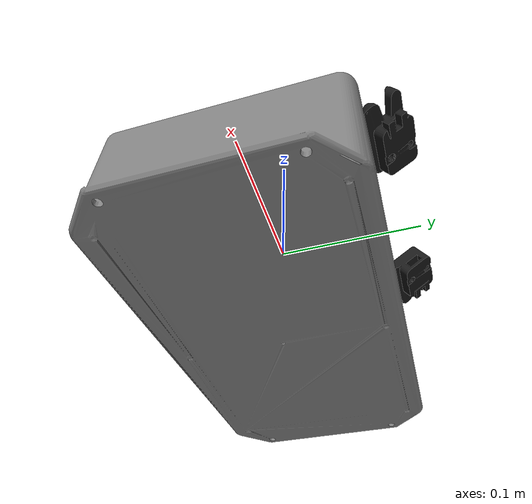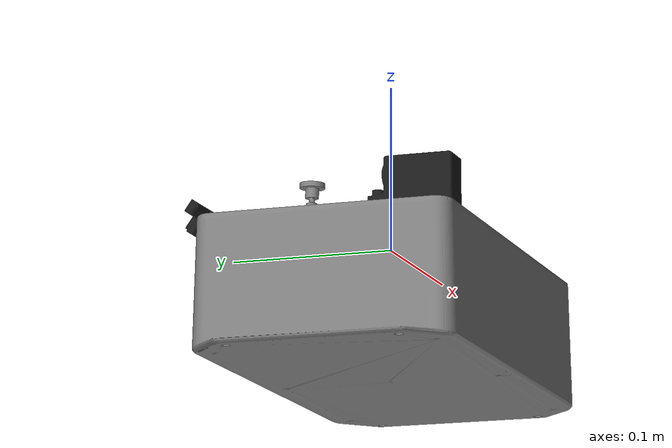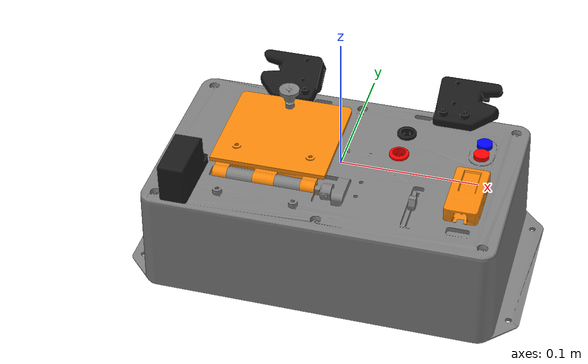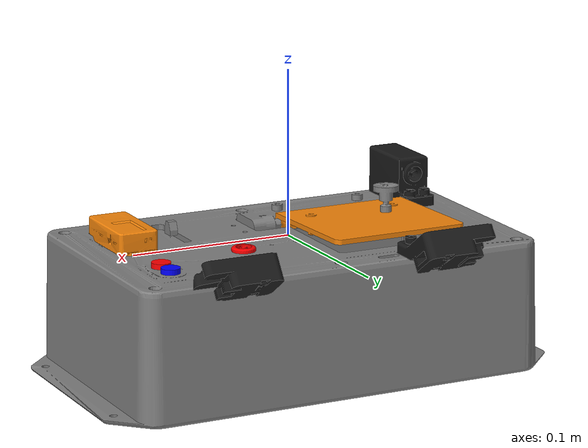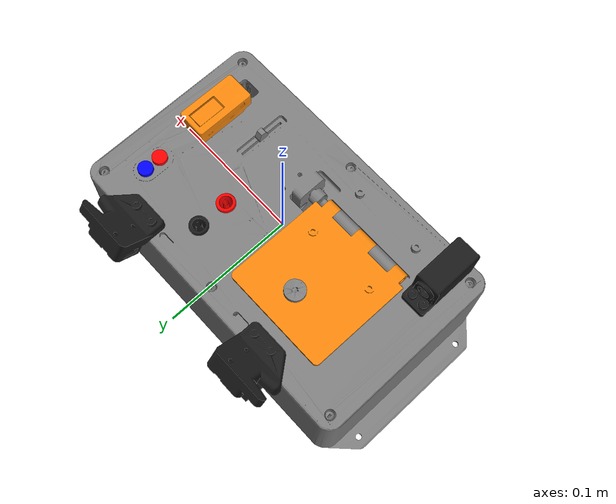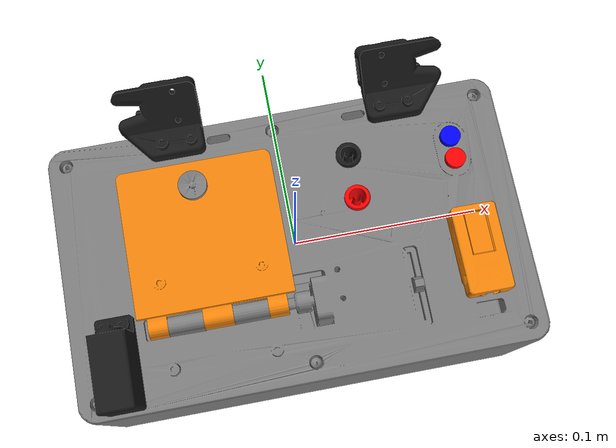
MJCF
<?xml version="1.0" ?>
<mujoco model="task_board_main">
	<compiler meshdir="task_board/meshes" texturedir="task_board/textures" angle="radian" autolimits="true" balanceinertia="true" />
	<default>
		<default class="task_board_visual">
			<geom contype="0" conaffinity="0"/>
		</default>
		<default class="task_board_collision">
			<geom rgba="0.9 0.9 0.9 1.0" group="3"/>
		</default>
	</default>
	<asset>
		<mesh name="TaskBoardBody" file="stl/TaskBoardMain.stl" scale="1.0 1.0 1.0"/>
		<mesh name="UCX_TaskBoardBody_001" file="stl/UCX_TaskBoardMain_001.stl" scale="1.0 1.0 1.0"/>
		<mesh name="UCX_TaskBoardBody_002" file="stl/UCX_TaskBoardMain_002.stl" scale="1.0 1.0 1.0"/>
		<mesh name="UCX_TaskBoardBody_003" file="stl/UCX_TaskBoardMain_003.stl" scale="1.0 1.0 1.0"/>
		<mesh name="UCX_TaskBoardBody_004" file="stl/UCX_TaskBoardMain_004.stl" scale="1.0 1.0 1.0"/>
		<mesh name="UCX_TaskBoardBody_005" file="stl/UCX_TaskBoardMain_005.stl" scale="1.0 1.0 1.0"/>
		<mesh name="UCX_TaskBoardBody_006" file="stl/UCX_TaskBoardMain_006.stl" scale="1.0 1.0 1.0"/>
		<mesh name="UCX_TaskBoardBody_007" file="stl/UCX_TaskBoardMain_007.stl" scale="1.0 1.0 1.0"/>
		<mesh name="UCX_TaskBoardBody_008" file="stl/UCX_TaskBoardMain_008.stl" scale="1.0 1.0 1.0"/>
		<mesh name="UCX_TaskBoardBody_009" file="stl/UCX_TaskBoardMain_009.stl" scale="1.0 1.0 1.0"/>
		<mesh name="UCX_TaskBoardBody_010" file="stl/UCX_TaskBoardMain_010.stl" scale="1.0 1.0 1.0"/>
		<mesh name="UCX_TaskBoardBody_011" file="stl/UCX_TaskBoardMain_011.stl" scale="1.0 1.0 1.0"/>
		<mesh name="UCX_TaskBoardBody_012" file="stl/UCX_TaskBoardMain_012.stl" scale="1.0 1.0 1.0"/>
		<mesh name="UCX_TaskBoardBody_013" file="stl/UCX_TaskBoardMain_013.stl" scale="1.0 1.0 1.0"/>
		<mesh name="UCX_TaskBoardBody_014" file="stl/UCX_TaskBoardMain_014.stl" scale="1.0 1.0 1.0"/>
		<mesh name="UCX_TaskBoardBody_015" file="stl/UCX_TaskBoardMain_015.stl" scale="1.0 1.0 1.0"/>
		<mesh name="UCX_TaskBoardBody_016" file="stl/UCX_TaskBoardMain_016.stl" scale="1.0 1.0 1.0"/>
		<mesh name="UCX_TaskBoardBody_017" file="stl/UCX_TaskBoardMain_017.stl" scale="1.0 1.0 1.0"/>
		<mesh name="UCX_TaskBoardBody_018" file="stl/UCX_TaskBoardMain_018.stl" scale="1.0 1.0 1.0"/>
		<mesh name="UCX_TaskBoardBody_019" file="stl/UCX_TaskBoardMain_019.stl" scale="1.0 1.0 1.0"/>
		<mesh name="UCX_TaskBoardBody_020" file="stl/UCX_TaskBoardMain_020.stl" scale="1.0 1.0 1.0"/>
		<mesh name="UCX_TaskBoardBody_021" file="stl/UCX_TaskBoardMain_021.stl" scale="1.0 1.0 1.0"/>
		<mesh name="UCX_TaskBoardBody_022" file="stl/UCX_TaskBoardMain_022.stl" scale="1.0 1.0 1.0"/>
		<mesh name="UCX_TaskBoardBody_023" file="stl/UCX_TaskBoardMain_023.stl" scale="1.0 1.0 1.0"/>
		<mesh name="UCX_TaskBoardBody_024" file="stl/UCX_TaskBoardMain_024.stl" scale="1.0 1.0 1.0"/>
		<mesh name="TaskBoardM5StickC" file="stl/TaskBoardM5StickC.stl" scale="1.0 1.0 1.0"/>
		<mesh name="UCX_TaskBoardM5StickC_001" file="stl/UCX_TaskBoardM5StickC_001.stl" scale="1.0 1.0 1.0"/>
		<mesh name="TaskBoardBananaPlug" file="stl/TaskBoardBananaPlug.stl" scale="1.0 1.0 1.0"/>
		<mesh name="UCX_TaskBoardHoleSide_001" file="stl/UCX_TaskBoardHoleSide_001.stl" scale="1.0 1.0 1.0"/>
		<mesh name="TaskBoardSlider" file="stl/TaskBoardSlider.stl" scale="1.0 1.0 1.0"/>
		<mesh name="UCX_TaskBoardSlider_001" file="stl/UCX_TaskBoardSlider_001.stl" scale="1.0 1.0 1.0"/>
		<mesh name="TaskBoardCableWrapPostLeft" file="stl/TaskBoardCableWrapPostLeft.stl" scale="1.0 1.0 1.0"/>
		<mesh name="UCX_TaskBoardCableWrapPostLeft_001" file="stl/UCX_TaskBoardCableWrapPostLeft_001.stl" scale="1.0 1.0 1.0"/>
		<mesh name="UCX_TaskBoardCableWrapPostLeft_002" file="stl/UCX_TaskBoardCableWrapPostLeft_002.stl" scale="1.0 1.0 1.0"/>
		<mesh name="UCX_TaskBoardCableWrapPostLeft_003" file="stl/UCX_TaskBoardCableWrapPostLeft_003.stl" scale="1.0 1.0 1.0"/>
		<mesh name="UCX_TaskBoardCableWrapPostLeft_004" file="stl/UCX_TaskBoardCableWrapPostLeft_004.stl" scale="1.0 1.0 1.0"/>
		<mesh name="UCX_TaskBoardCableWrapPostLeft_005" file="stl/UCX_TaskBoardCableWrapPostLeft_005.stl" scale="1.0 1.0 1.0"/>
		<mesh name="UCX_TaskBoardCableWrapPostLeft_006" file="stl/UCX_TaskBoardCableWrapPostLeft_006.stl" scale="1.0 1.0 1.0"/>
		<mesh name="UCX_TaskBoardCableWrapPostLeft_007" file="stl/UCX_TaskBoardCableWrapPostLeft_007.stl" scale="1.0 1.0 1.0"/>
		<mesh name="UCX_TaskBoardCableWrapPostLeft_008" file="stl/UCX_TaskBoardCableWrapPostLeft_008.stl" scale="1.0 1.0 1.0"/>
		<mesh name="UCX_TaskBoardCableWrapPostLeft_009" file="stl/UCX_TaskBoardCableWrapPostLeft_009.stl" scale="1.0 1.0 1.0"/>
		<mesh name="UCX_TaskBoardCableWrapPostLeft_010" file="stl/UCX_TaskBoardCableWrapPostLeft_010.stl" scale="1.0 1.0 1.0"/>
		<mesh name="UCX_TaskBoardCableWrapPostLeft_011" file="stl/UCX_TaskBoardCableWrapPostLeft_011.stl" scale="1.0 1.0 1.0"/>
		<mesh name="TaskBoardCableWrapPostRight" file="stl/TaskBoardCableWrapPostRight.stl" scale="1.0 1.0 1.0"/>
		<mesh name="UCX_TaskBoardCableWrapPostRight_001" file="stl/UCX_TaskBoardCableWrapPostRight_001.stl" scale="1.0 1.0 1.0"/>
		<mesh name="UCX_TaskBoardCableWrapPostRight_002" file="stl/UCX_TaskBoardCableWrapPostRight_002.stl" scale="1.0 1.0 1.0"/>
		<mesh name="UCX_TaskBoardCableWrapPostRight_003" file="stl/UCX_TaskBoardCableWrapPostRight_003.stl" scale="1.0 1.0 1.0"/>
		<mesh name="UCX_TaskBoardCableWrapPostRight_004" file="stl/UCX_TaskBoardCableWrapPostRight_004.stl" scale="1.0 1.0 1.0"/>
		<mesh name="UCX_TaskBoardCableWrapPostRight_005" file="stl/UCX_TaskBoardCableWrapPostRight_005.stl" scale="1.0 1.0 1.0"/>
		<mesh name="UCX_TaskBoardCableWrapPostRight_006" file="stl/UCX_TaskBoardCableWrapPostRight_006.stl" scale="1.0 1.0 1.0"/>
		<mesh name="UCX_TaskBoardCableWrapPostRight_007" file="stl/UCX_TaskBoardCableWrapPostRight_007.stl" scale="1.0 1.0 1.0"/>
		<mesh name="UCX_TaskBoardCableWrapPostRight_008" file="stl/UCX_TaskBoardCableWrapPostRight_008.stl" scale="1.0 1.0 1.0"/>
		<mesh name="UCX_TaskBoardCableWrapPostRight_009" file="stl/UCX_TaskBoardCableWrapPostRight_009.stl" scale="1.0 1.0 1.0"/>
		<mesh name="UCX_TaskBoardCableWrapPostRight_010" file="stl/UCX_TaskBoardCableWrapPostRight_010.stl" scale="1.0 1.0 1.0"/>
		<mesh name="UCX_TaskBoardCableWrapPostRight_011" file="stl/UCX_TaskBoardCableWrapPostRight_011.stl" scale="1.0 1.0 1.0"/>
		<mesh name="TaskBoardLid" file="stl/TaskBoardLid.stl" scale="1.0 1.0 1.0"/>
		<mesh name="UCX_TaskBoardLid_001" file="stl/UCX_TaskBoardLid_001.stl" scale="1.0 1.0 1.0"/>
		<mesh name="TaskBoardLidKnob" file="stl/TaskBoardLidKnob.stl" scale="1.0 1.0 1.0"/>
		<mesh name="TaskBoardBananaPlugPort" file="stl/TaskBoardBananaPlugPort.stl" scale="1.0 1.0 1.0"/>
		<mesh name="UCX_TaskBoardBananaPlugPort_001" file="stl/UCX_TaskBoardBananaPlugPort_001.stl" scale="1.0 1.0 1.0"/>
		<mesh name="UCX_TaskBoardBananaPlugPort_002" file="stl/UCX_TaskBoardBananaPlugPort_002.stl" scale="1.0 1.0 1.0"/>
		<mesh name="UCX_TaskBoardBananaPlugPort_003" file="stl/UCX_TaskBoardBananaPlugPort_003.stl" scale="1.0 1.0 1.0"/>
		<mesh name="UCX_TaskBoardBananaPlugPort_004" file="stl/UCX_TaskBoardBananaPlugPort_004.stl" scale="1.0 1.0 1.0"/>
		<mesh name="UCX_TaskBoardBananaPlugPort_005" file="stl/UCX_TaskBoardBananaPlugPort_005.stl" scale="1.0 1.0 1.0"/>
		<mesh name="UCX_TaskBoardBananaPlugPort_006" file="stl/UCX_TaskBoardBananaPlugPort_006.stl" scale="1.0 1.0 1.0"/>
	</asset>
	<worldbody>
		<body name="task_board_main" pos="0.0 0.0 0.0" quat="1.0 0.0 0.0 0.0">
			<body name="task_board_body" pos="0.0 0.0 0.0" quat="1.0 0.0 0.0 0.0">
				<inertial mass="7.616941928863525" pos="-0.0011780796339735389 -3.9309339626925066e-05 -0.039935238659381866" quat="0.00119794683996588 0.6997284293174744 0.007045551668852568 0.7143731713294983" diaginertia="0.05582557991147041 0.04489736631512642 0.018900347873568535"/>
				<geom name="task_board_body_visual" type="mesh" pos="-0.0013512435834854841 -4.9608697736402974e-05 -0.039861757308244705" quat="0.0014318180037662387 0.6994011998176575 0.007516392506659031 0.7146883606910706" mesh="TaskBoardBody" rgba="0.5 0.5 0.5 1.0" class="task_board_visual"/>
				<geom name="task_board_body_collision_001" type="mesh" pos="-0.0006921887979842722 0.0005634986446239054 -0.07817842066287994" quat="0.0 0.7071067690849304 0.0 0.7071067690849304" mesh="UCX_TaskBoardBody_001" class="task_board_collision"/>
				<geom name="task_board_body_collision_002" type="mesh" pos="-0.0007403581403195858 -0.07277718186378479 -0.040174443274736404" quat="0.5065849423408508 0.4933449923992157 0.506567120552063 0.49332764744758606" mesh="UCX_TaskBoardBody_002" class="task_board_collision"/>
				<geom name="task_board_body_collision_003" type="mesh" pos="-0.0007051100837998092 0.07390077412128448 -0.04017476737499237" quat="0.49333223700523376 0.5065765380859375 0.4933401346206665 0.5065757632255554" mesh="UCX_TaskBoardBody_003" class="task_board_collision"/>
				<geom name="task_board_body_collision_004" type="mesh" pos="-0.1272374540567398 0.000563445792067796 -0.040238115936517715" quat="0.7070314288139343 0.7070314288139343 0.010323220863938332 -0.010323220863938332" mesh="UCX_TaskBoardBody_004" class="task_board_collision"/>
				<geom name="task_board_body_collision_005" type="mesh" pos="0.12583637237548828 0.000556890678126365 -0.04023807868361473" quat="0.7070314288139343 0.7070314288139343 -0.010323233902454376 0.010323233902454376" mesh="UCX_TaskBoardBody_005" class="task_board_collision"/>
				<geom name="task_board_body_collision_006" type="mesh" pos="0.09508127719163895 0.0005627145292237401 -0.0016510002315044403" quat="0.49999669194221497 0.5000033378601074 -0.49999669194221497 0.5000033378601074" mesh="UCX_TaskBoardBody_006" class="task_board_collision"/>
				<geom name="task_board_body_collision_007" type="mesh" pos="-0.10720948874950409 0.0005629970692098141 -0.0016510002315044403" quat="0.500001072883606 0.49999892711639404 -0.500001072883606 0.49999892711639404" mesh="UCX_TaskBoardBody_007" class="task_board_collision"/>
				<geom name="task_board_body_collision_008" type="mesh" pos="-0.08628399670124054 0.025334490463137627 -0.0016510002315044403" quat="0.7071067690849304 0.7071067690849304 0.0 0.0" mesh="UCX_TaskBoardBody_008" class="task_board_collision"/>
				<geom name="task_board_body_collision_009" type="mesh" pos="-0.04828399792313576 -0.056859493255615234 -0.0016510002315044403" quat="0.0 0.7071067690849304 0.0 0.7071067690849304" mesh="UCX_TaskBoardBody_009" class="task_board_collision"/>
				<geom name="task_board_body_collision_010" type="mesh" pos="0.02357950061559677 -0.06173449009656906 -0.0016510002315044403" quat="0.0 0.7071067690849304 0.0 0.7071067690849304" mesh="UCX_TaskBoardBody_010" class="task_board_collision"/>
				<geom name="task_board_body_collision_011" type="mesh" pos="0.06044299528002739 -0.06620799005031586 -0.0016510002315044403" quat="0.5 0.5 -0.5 0.5" mesh="UCX_TaskBoardBody_011" class="task_board_collision"/>
				<geom name="task_board_body_collision_012" type="mesh" pos="0.034579500555992126 -0.032332997769117355 -0.0016510002315044403" quat="0.0 0.7071067690849304 0.0 0.7071067690849304" mesh="UCX_TaskBoardBody_012" class="task_board_collision"/>
				<geom name="task_board_body_collision_013" type="mesh" pos="0.023579496890306473 -0.002088000299409032 -0.0016510002315044403" quat="0.0 0.7071067690849304 0.0 0.7071067690849304" mesh="UCX_TaskBoardBody_013" class="task_board_collision"/>
				<geom name="task_board_body_collision_014" type="mesh" pos="0.06044299900531769 0.031991489231586456 -0.0016510002315044403" quat="0.5 0.5 -0.5 0.5" mesh="UCX_TaskBoardBody_014" class="task_board_collision"/>
				<geom name="task_board_body_collision_015" type="mesh" pos="0.023579496890306473 0.06345998495817184 -0.0016510002315044403" quat="0.0 0.7071067690849304 0.0 0.7071067690849304" mesh="UCX_TaskBoardBody_015" class="task_board_collision"/>
				<geom name="task_board_body_collision_016" type="mesh" pos="0.023579496890306473 0.03140699863433838 -0.0016510002315044403" quat="0.0 0.7071067690849304 0.0 0.7071067690849304" mesh="UCX_TaskBoardBody_016" class="task_board_collision"/>
				<geom name="task_board_body_collision_017" type="mesh" pos="0.050563499331474304 0.04390700161457062 -0.0016510002315044403" quat="0.5 0.5 -0.5 0.5" mesh="UCX_TaskBoardBody_017" class="task_board_collision"/>
				<geom name="task_board_body_collision_018" type="mesh" pos="0.050563499331474304 0.01890699751675129 -0.0016510002315044403" quat="0.5 0.5 -0.5 0.5" mesh="UCX_TaskBoardBody_018" class="task_board_collision"/>
				<geom name="task_board_body_collision_019" type="mesh" pos="0.01145949773490429 0.01890699751675129 -0.0016510002315044403" quat="0.0 0.7071067690849304 0.0 0.7071067690849304" mesh="UCX_TaskBoardBody_019" class="task_board_collision"/>
				<geom name="task_board_body_collision_020" type="mesh" pos="0.01145949773490429 0.04390700161457062 -0.0016510002315044403" quat="0.0 0.7071067690849304 0.0 0.7071067690849304" mesh="UCX_TaskBoardBody_020" class="task_board_collision"/>
				<geom name="task_board_body_collision_021" type="mesh" pos="-0.047283995896577835 0.06283999979496002 -0.0016510002315044403" quat="0.0 0.7071067690849304 0.0 0.7071067690849304" mesh="UCX_TaskBoardBody_021" class="task_board_collision"/>
				<geom name="task_board_body_collision_022" type="mesh" pos="0.008515998721122742 -0.03233299404382706 -0.010401993989944458" quat="1.0 0.0 0.0 0.0" mesh="UCX_TaskBoardBody_022" class="task_board_collision"/>
				<geom name="task_board_body_collision_023" type="mesh" pos="0.000116005539894104 -0.03203300014138222 -0.0019019993487745523" quat="1.0 0.0 0.0 0.0" mesh="UCX_TaskBoardBody_023" class="task_board_collision"/>
				<geom name="task_board_body_collision_024" type="mesh" pos="-0.010883995331823826 -0.03203300014138222 -0.0019019993487745523" quat="0.5 0.5 0.5 0.5" mesh="UCX_TaskBoardBody_024" class="task_board_collision"/>
			</body>
			<body name="task_board_banana_plug_black" pos="0.03844299912452698 0.04390700161457062 0.0" quat="1.0 0.0 0.0 0.0">
				<inertial mass="0.004504608456045389" pos="1.5940020858806747e-08 -2.135486631971162e-08 -0.009129293262958527" quat="1.0 0.0 0.0 0.0" diaginertia="2.1914435421876988e-07 2.1908198277742486e-07 7.183392369825015e-08"/>
				<geom name="task_board_banana_plug_black_visual" type="mesh" pos="1.5940020858806747e-08 -2.135486631971162e-08 -0.009129293262958527" quat="1.0 0.0 0.0 0.0" mesh="TaskBoardBananaPlug" rgba="0.1 0.1 0.1 1.0" class="task_board_visual"/>
				<body name="task_board_banana_plug_black_hole" pos="0.0 0.0 0.0024999999441206455" quat="1.0 0.0 0.0 0.0">
					<inertial mass="0.002106040483340621" pos="0.0 3.896236269071907e-19 -0.011749510653316975" quat="1.0 0.0 0.0 0.0" diaginertia="1.3173702484436944e-07 1.3173702484436944e-07 7.209348495962331e-08"/>
					<geom name="task_board_banana_plug_hole_black_collision_001" type="mesh" pos="0.00579674169421196 -7.939510737742239e-07 -0.011749510653316975" quat="0.7071067690849304 -0.0002342794177820906 -0.0002342794177820906 0.7071067690849304" mesh="UCX_TaskBoardHoleSide_001" class="task_board_collision"/>
					<geom name="task_board_banana_plug_hole_black_collision_002" type="mesh" pos="0.005685513839125633 0.0011301087215542793 -0.011749510653316975" quat="0.6343932747840881 -0.00021018792176619172 -0.0002561146975494921 0.7730103731155396" mesh="UCX_TaskBoardHoleSide_001" class="task_board_collision"/>
					<geom name="task_board_banana_plug_hole_black_collision_003" type="mesh" pos="0.005355795845389366 0.002217580797150731 -0.011749510653316975" quat="0.5555704236030579 -0.00018407223979011178 -0.00027548341313377023 0.8314694166183472" mesh="UCX_TaskBoardHoleSide_001" class="task_board_collision"/>
					<geom name="task_board_banana_plug_hole_black_collision_004" type="mesh" pos="0.004820253234356642 0.0032198410481214523 -0.011749510653316975" quat="0.4713963568210602 -0.00015618358156643808 -0.0002921992272604257 0.8819214105606079" mesh="UCX_TaskBoardHoleSide_001" class="task_board_collision"/>
					<geom name="task_board_banana_plug_hole_black_collision_005" type="mesh" pos="0.004099481739103794 0.004098349250853062 -0.011749510653316975" quat="0.3826839327812195 -0.00012679128849413246 -0.0003061007591895759 0.9238792657852173" mesh="UCX_TaskBoardHoleSide_001" class="task_board_collision"/>
					<geom name="task_board_banana_plug_hole_black_collision_006" type="mesh" pos="0.0032211539801210165 0.004819375928491354 -0.011749510653316975" quat="0.29028430581092834 -9.617733303457499e-05 -0.00031705459696240723 0.9569404125213623" mesh="UCX_TaskBoardHoleSide_001" class="task_board_collision"/>
					<geom name="task_board_banana_plug_hole_black_collision_007" type="mesh" pos="0.0022190548479557037 0.005355185363441706 -0.011749510653316975" quat="0.19509071111679077 -6.46376793156378e-05 -0.00032495486084371805 0.9807851314544678" mesh="UCX_TaskBoardHoleSide_001" class="task_board_collision"/>
					<geom name="task_board_banana_plug_hole_black_collision_008" type="mesh" pos="0.00113166612572968 0.005685204174369574 -0.011749510653316975" quat="0.09801706671714783 -3.247512722737156e-05 -0.0003297257353551686 0.9951846599578857" mesh="UCX_TaskBoardHoleSide_001" class="task_board_collision"/>
					<geom name="task_board_banana_plug_hole_black_collision_009" type="mesh" pos="7.939510737742239e-07 0.00579674169421196 -0.011749510653316975" quat="0.0 0.0 -0.0003313211491331458 0.9999999403953552" mesh="UCX_TaskBoardHoleSide_001" class="task_board_collision"/>
					<geom name="task_board_banana_plug_hole_black_collision_010" type="mesh" pos="-0.0011301087215542793 0.005685513839125633 -0.011749510653316975" quat="-0.09801706671714783 3.247512722737156e-05 -0.0003297257353551686 0.9951846599578857" mesh="UCX_TaskBoardHoleSide_001" class="task_board_collision"/>
					<geom name="task_board_banana_plug_hole_black_collision_011" type="mesh" pos="-0.0022175877820700407 0.005355793051421642 -0.011749510653316975" quat="-0.19509071111679077 6.46376793156378e-05 -0.00032495486084371805 0.9807851314544678" mesh="UCX_TaskBoardHoleSide_001" class="task_board_collision"/>
					<geom name="task_board_banana_plug_hole_black_collision_012" type="mesh" pos="-0.0032198335975408554 0.004820257890969515 -0.011749510653316975" quat="-0.29028430581092834 9.617733303457499e-05 -0.00031705459696240723 0.9569404125213623" mesh="UCX_TaskBoardHoleSide_001" class="task_board_collision"/>
					<geom name="task_board_banana_plug_hole_black_collision_013" type="mesh" pos="-0.004098358564078808 0.004099471960216761 -0.011749510653316975" quat="-0.3826839327812195 0.00012679128849413246 -0.0003061007591895759 0.9238792657852173" mesh="UCX_TaskBoardHoleSide_001" class="task_board_collision"/>
					<geom name="task_board_banana_plug_hole_black_collision_014" type="mesh" pos="-0.004819370806217194 0.0032211611978709698 -0.011749510653316975" quat="-0.4713963568210602 0.00015618358156643808 -0.0002921992272604257 0.8819214105606079" mesh="UCX_TaskBoardHoleSide_001" class="task_board_collision"/>
					<geom name="task_board_banana_plug_hole_black_collision_015" type="mesh" pos="-0.0053551881574094296 0.0022190476302057505 -0.011749510653316975" quat="-0.5555704236030579 0.00018407223979011178 -0.00027548341313377023 0.8314694166183472" mesh="UCX_TaskBoardHoleSide_001" class="task_board_collision"/>
					<geom name="task_board_banana_plug_hole_black_collision_016" type="mesh" pos="-0.005685204174369574 0.00113166612572968 -0.011749510653316975" quat="-0.6343932747840881 0.00021018792176619172 -0.0002561146975494921 0.7730103731155396" mesh="UCX_TaskBoardHoleSide_001" class="task_board_collision"/>
					<geom name="task_board_banana_plug_hole_black_collision_017" type="mesh" pos="-0.00579674169421196 7.939510737742239e-07 -0.011749510653316975" quat="-0.7071067690849304 0.0002342794177820906 -0.0002342794177820906 0.7071067690849304" mesh="UCX_TaskBoardHoleSide_001" class="task_board_collision"/>
					<geom name="task_board_banana_plug_hole_black_collision_018" type="mesh" pos="-0.005685513839125633 -0.0011301087215542793 -0.011749510653316975" quat="-0.7730103731155396 0.0002561146975494921 -0.00021018792176619172 0.6343932747840881" mesh="UCX_TaskBoardHoleSide_001" class="task_board_collision"/>
					<geom name="task_board_banana_plug_hole_black_collision_019" type="mesh" pos="-0.005355795845389366 -0.002217580797150731 -0.011749510653316975" quat="-0.8314694166183472 0.00027548341313377023 -0.00018407223979011178 0.5555704236030579" mesh="UCX_TaskBoardHoleSide_001" class="task_board_collision"/>
					<geom name="task_board_banana_plug_hole_black_collision_020" type="mesh" pos="-0.004820253234356642 -0.0032198410481214523 -0.011749510653316975" quat="-0.8819214105606079 0.0002921992272604257 -0.00015618358156643808 0.4713963568210602" mesh="UCX_TaskBoardHoleSide_001" class="task_board_collision"/>
					<geom name="task_board_banana_plug_hole_black_collision_021" type="mesh" pos="-0.004099481739103794 -0.004098349250853062 -0.011749510653316975" quat="-0.9238792657852173 0.0003061007591895759 -0.00012679128849413246 0.3826839327812195" mesh="UCX_TaskBoardHoleSide_001" class="task_board_collision"/>
					<geom name="task_board_banana_plug_hole_black_collision_022" type="mesh" pos="-0.0032211539801210165 -0.004819375928491354 -0.011749510653316975" quat="-0.9569404125213623 0.00031705459696240723 -9.617733303457499e-05 0.29028430581092834" mesh="UCX_TaskBoardHoleSide_001" class="task_board_collision"/>
					<geom name="task_board_banana_plug_hole_black_collision_023" type="mesh" pos="-0.0022190548479557037 -0.005355185363441706 -0.011749510653316975" quat="-0.9807851314544678 0.00032495486084371805 -6.46376793156378e-05 0.19509071111679077" mesh="UCX_TaskBoardHoleSide_001" class="task_board_collision"/>
					<geom name="task_board_banana_plug_hole_black_collision_024" type="mesh" pos="-0.00113166612572968 -0.005685204174369574 -0.011749510653316975" quat="-0.9951846599578857 0.0003297257353551686 -3.247512722737156e-05 0.09801706671714783" mesh="UCX_TaskBoardHoleSide_001" class="task_board_collision"/>
					<geom name="task_board_banana_plug_hole_black_collision_025" type="mesh" pos="-7.939510737742239e-07 -0.00579674169421196 -0.011749510653316975" quat="-0.9999999403953552 0.0003313211491331458 0.0 0.0" mesh="UCX_TaskBoardHoleSide_001" class="task_board_collision"/>
					<geom name="task_board_banana_plug_hole_black_collision_026" type="mesh" pos="0.0011301087215542793 -0.005685513839125633 -0.011749510653316975" quat="-0.9951846599578857 0.0003297257353551686 3.247512722737156e-05 -0.09801706671714783" mesh="UCX_TaskBoardHoleSide_001" class="task_board_collision"/>
					<geom name="task_board_banana_plug_hole_black_collision_027" type="mesh" pos="0.0022175877820700407 -0.005355793051421642 -0.011749510653316975" quat="-0.9807851314544678 0.00032495486084371805 6.46376793156378e-05 -0.19509071111679077" mesh="UCX_TaskBoardHoleSide_001" class="task_board_collision"/>
					<geom name="task_board_banana_plug_hole_black_collision_028" type="mesh" pos="0.0032198335975408554 -0.004820257890969515 -0.011749510653316975" quat="-0.9569404125213623 0.00031705459696240723 9.617733303457499e-05 -0.29028430581092834" mesh="UCX_TaskBoardHoleSide_001" class="task_board_collision"/>
					<geom name="task_board_banana_plug_hole_black_collision_029" type="mesh" pos="0.004098358564078808 -0.004099471960216761 -0.011749510653316975" quat="-0.9238792657852173 0.0003061007591895759 0.00012679128849413246 -0.3826839327812195" mesh="UCX_TaskBoardHoleSide_001" class="task_board_collision"/>
					<geom name="task_board_banana_plug_hole_black_collision_030" type="mesh" pos="0.004819370806217194 -0.0032211611978709698 -0.011749510653316975" quat="-0.8819214105606079 0.0002921992272604257 0.00015618358156643808 -0.4713963568210602" mesh="UCX_TaskBoardHoleSide_001" class="task_board_collision"/>
					<geom name="task_board_banana_plug_hole_black_collision_031" type="mesh" pos="0.0053551881574094296 -0.0022190476302057505 -0.011749510653316975" quat="-0.8314694166183472 0.00027548341313377023 0.00018407223979011178 -0.5555704236030579" mesh="UCX_TaskBoardHoleSide_001" class="task_board_collision"/>
					<geom name="task_board_banana_plug_hole_black_collision_032" type="mesh" pos="0.005685204174369574 -0.00113166612572968 -0.011749510653316975" quat="-0.7730103731155396 0.0002561146975494921 0.00021018792176619172 -0.6343932747840881" mesh="UCX_TaskBoardHoleSide_001" class="task_board_collision"/>
				</body>
			</body>
			<body name="task_board_banana_plug_red" pos="0.03844299912452698 0.01890699937939644 0.0" quat="1.0 0.0 0.0 0.0">
				<inertial mass="0.004504608456045389" pos="1.5940020858806747e-08 -2.135486631971162e-08 -0.009129293262958527" quat="1.0 0.0 0.0 0.0" diaginertia="2.1914435421876988e-07 2.1908198277742486e-07 7.183392369825015e-08"/>
				<geom name="task_board_banana_plug_red_visual" type="mesh" pos="1.5940020858806747e-08 -2.135486631971162e-08 -0.009129293262958527" quat="1.0 0.0 0.0 0.0" mesh="TaskBoardBananaPlug" rgba="1.0 0.0 0.0 1.0" class="task_board_visual"/>
				<body name="task_board_banana_plug_red_hole" pos="0.0 0.0 0.0024999999441206455" quat="1.0 0.0 0.0 0.0">
					<inertial mass="0.002106040483340621" pos="0.0 3.896236269071907e-19 -0.011749510653316975" quat="1.0 0.0 0.0 0.0" diaginertia="1.3173702484436944e-07 1.3173702484436944e-07 7.209348495962331e-08"/>
					<geom name="task_board_banana_plug_hole_red_collision_001" type="mesh" pos="0.00579674169421196 -7.939510737742239e-07 -0.011749510653316975" quat="0.7071067690849304 -0.0002342794177820906 -0.0002342794177820906 0.7071067690849304" mesh="UCX_TaskBoardHoleSide_001" class="task_board_collision"/>
					<geom name="task_board_banana_plug_hole_red_collision_002" type="mesh" pos="0.005685513839125633 0.0011301087215542793 -0.011749510653316975" quat="0.6343932747840881 -0.00021018792176619172 -0.0002561146975494921 0.7730103731155396" mesh="UCX_TaskBoardHoleSide_001" class="task_board_collision"/>
					<geom name="task_board_banana_plug_hole_red_collision_003" type="mesh" pos="0.005355795845389366 0.002217580797150731 -0.011749510653316975" quat="0.5555704236030579 -0.00018407223979011178 -0.00027548341313377023 0.8314694166183472" mesh="UCX_TaskBoardHoleSide_001" class="task_board_collision"/>
					<geom name="task_board_banana_plug_hole_red_collision_004" type="mesh" pos="0.004820253234356642 0.0032198410481214523 -0.011749510653316975" quat="0.4713963568210602 -0.00015618358156643808 -0.0002921992272604257 0.8819214105606079" mesh="UCX_TaskBoardHoleSide_001" class="task_board_collision"/>
					<geom name="task_board_banana_plug_hole_red_collision_005" type="mesh" pos="0.004099481739103794 0.004098349250853062 -0.011749510653316975" quat="0.3826839327812195 -0.00012679128849413246 -0.0003061007591895759 0.9238792657852173" mesh="UCX_TaskBoardHoleSide_001" class="task_board_collision"/>
					<geom name="task_board_banana_plug_hole_red_collision_006" type="mesh" pos="0.0032211539801210165 0.004819375928491354 -0.011749510653316975" quat="0.29028430581092834 -9.617733303457499e-05 -0.00031705459696240723 0.9569404125213623" mesh="UCX_TaskBoardHoleSide_001" class="task_board_collision"/>
					<geom name="task_board_banana_plug_hole_red_collision_007" type="mesh" pos="0.0022190548479557037 0.005355185363441706 -0.011749510653316975" quat="0.19509071111679077 -6.46376793156378e-05 -0.00032495486084371805 0.9807851314544678" mesh="UCX_TaskBoardHoleSide_001" class="task_board_collision"/>
					<geom name="task_board_banana_plug_hole_red_collision_008" type="mesh" pos="0.00113166612572968 0.005685204174369574 -0.011749510653316975" quat="0.09801706671714783 -3.247512722737156e-05 -0.0003297257353551686 0.9951846599578857" mesh="UCX_TaskBoardHoleSide_001" class="task_board_collision"/>
					<geom name="task_board_banana_plug_hole_red_collision_009" type="mesh" pos="7.939510737742239e-07 0.00579674169421196 -0.011749510653316975" quat="0.0 0.0 -0.0003313211491331458 0.9999999403953552" mesh="UCX_TaskBoardHoleSide_001" class="task_board_collision"/>
					<geom name="task_board_banana_plug_hole_red_collision_010" type="mesh" pos="-0.0011301087215542793 0.005685513839125633 -0.011749510653316975" quat="-0.09801706671714783 3.247512722737156e-05 -0.0003297257353551686 0.9951846599578857" mesh="UCX_TaskBoardHoleSide_001" class="task_board_collision"/>
					<geom name="task_board_banana_plug_hole_red_collision_011" type="mesh" pos="-0.0022175877820700407 0.005355793051421642 -0.011749510653316975" quat="-0.19509071111679077 6.46376793156378e-05 -0.00032495486084371805 0.9807851314544678" mesh="UCX_TaskBoardHoleSide_001" class="task_board_collision"/>
					<geom name="task_board_banana_plug_hole_red_collision_012" type="mesh" pos="-0.0032198335975408554 0.004820257890969515 -0.011749510653316975" quat="-0.29028430581092834 9.617733303457499e-05 -0.00031705459696240723 0.9569404125213623" mesh="UCX_TaskBoardHoleSide_001" class="task_board_collision"/>
					<geom name="task_board_banana_plug_hole_red_collision_013" type="mesh" pos="-0.004098358564078808 0.004099471960216761 -0.011749510653316975" quat="-0.3826839327812195 0.00012679128849413246 -0.0003061007591895759 0.9238792657852173" mesh="UCX_TaskBoardHoleSide_001" class="task_board_collision"/>
					<geom name="task_board_banana_plug_hole_red_collision_014" type="mesh" pos="-0.004819370806217194 0.0032211611978709698 -0.011749510653316975" quat="-0.4713963568210602 0.00015618358156643808 -0.0002921992272604257 0.8819214105606079" mesh="UCX_TaskBoardHoleSide_001" class="task_board_collision"/>
					<geom name="task_board_banana_plug_hole_red_collision_015" type="mesh" pos="-0.0053551881574094296 0.0022190476302057505 -0.011749510653316975" quat="-0.5555704236030579 0.00018407223979011178 -0.00027548341313377023 0.8314694166183472" mesh="UCX_TaskBoardHoleSide_001" class="task_board_collision"/>
					<geom name="task_board_banana_plug_hole_red_collision_016" type="mesh" pos="-0.005685204174369574 0.00113166612572968 -0.011749510653316975" quat="-0.6343932747840881 0.00021018792176619172 -0.0002561146975494921 0.7730103731155396" mesh="UCX_TaskBoardHoleSide_001" class="task_board_collision"/>
					<geom name="task_board_banana_plug_hole_red_collision_017" type="mesh" pos="-0.00579674169421196 7.939510737742239e-07 -0.011749510653316975" quat="-0.7071067690849304 0.0002342794177820906 -0.0002342794177820906 0.7071067690849304" mesh="UCX_TaskBoardHoleSide_001" class="task_board_collision"/>
					<geom name="task_board_banana_plug_hole_red_collision_018" type="mesh" pos="-0.005685513839125633 -0.0011301087215542793 -0.011749510653316975" quat="-0.7730103731155396 0.0002561146975494921 -0.00021018792176619172 0.6343932747840881" mesh="UCX_TaskBoardHoleSide_001" class="task_board_collision"/>
					<geom name="task_board_banana_plug_hole_red_collision_019" type="mesh" pos="-0.005355795845389366 -0.002217580797150731 -0.011749510653316975" quat="-0.8314694166183472 0.00027548341313377023 -0.00018407223979011178 0.5555704236030579" mesh="UCX_TaskBoardHoleSide_001" class="task_board_collision"/>
					<geom name="task_board_banana_plug_hole_red_collision_020" type="mesh" pos="-0.004820253234356642 -0.0032198410481214523 -0.011749510653316975" quat="-0.8819214105606079 0.0002921992272604257 -0.00015618358156643808 0.4713963568210602" mesh="UCX_TaskBoardHoleSide_001" class="task_board_collision"/>
					<geom name="task_board_banana_plug_hole_red_collision_021" type="mesh" pos="-0.004099481739103794 -0.004098349250853062 -0.011749510653316975" quat="-0.9238792657852173 0.0003061007591895759 -0.00012679128849413246 0.3826839327812195" mesh="UCX_TaskBoardHoleSide_001" class="task_board_collision"/>
					<geom name="task_board_banana_plug_hole_red_collision_022" type="mesh" pos="-0.0032211539801210165 -0.004819375928491354 -0.011749510653316975" quat="-0.9569404125213623 0.00031705459696240723 -9.617733303457499e-05 0.29028430581092834" mesh="UCX_TaskBoardHoleSide_001" class="task_board_collision"/>
					<geom name="task_board_banana_plug_hole_red_collision_023" type="mesh" pos="-0.0022190548479557037 -0.005355185363441706 -0.011749510653316975" quat="-0.9807851314544678 0.00032495486084371805 -6.46376793156378e-05 0.19509071111679077" mesh="UCX_TaskBoardHoleSide_001" class="task_board_collision"/>
					<geom name="task_board_banana_plug_hole_red_collision_024" type="mesh" pos="-0.00113166612572968 -0.005685204174369574 -0.011749510653316975" quat="-0.9951846599578857 0.0003297257353551686 -3.247512722737156e-05 0.09801706671714783" mesh="UCX_TaskBoardHoleSide_001" class="task_board_collision"/>
					<geom name="task_board_banana_plug_hole_red_collision_025" type="mesh" pos="-7.939510737742239e-07 -0.00579674169421196 -0.011749510653316975" quat="-0.9999999403953552 0.0003313211491331458 0.0 0.0" mesh="UCX_TaskBoardHoleSide_001" class="task_board_collision"/>
					<geom name="task_board_banana_plug_hole_red_collision_026" type="mesh" pos="0.0011301087215542793 -0.005685513839125633 -0.011749510653316975" quat="-0.9951846599578857 0.0003297257353551686 3.247512722737156e-05 -0.09801706671714783" mesh="UCX_TaskBoardHoleSide_001" class="task_board_collision"/>
					<geom name="task_board_banana_plug_hole_red_collision_027" type="mesh" pos="0.0022175877820700407 -0.005355793051421642 -0.011749510653316975" quat="-0.9807851314544678 0.00032495486084371805 6.46376793156378e-05 -0.19509071111679077" mesh="UCX_TaskBoardHoleSide_001" class="task_board_collision"/>
					<geom name="task_board_banana_plug_hole_red_collision_028" type="mesh" pos="0.0032198335975408554 -0.004820257890969515 -0.011749510653316975" quat="-0.9569404125213623 0.00031705459696240723 9.617733303457499e-05 -0.29028430581092834" mesh="UCX_TaskBoardHoleSide_001" class="task_board_collision"/>
					<geom name="task_board_banana_plug_hole_red_collision_029" type="mesh" pos="0.004098358564078808 -0.004099471960216761 -0.011749510653316975" quat="-0.9238792657852173 0.0003061007591895759 0.00012679128849413246 -0.3826839327812195" mesh="UCX_TaskBoardHoleSide_001" class="task_board_collision"/>
					<geom name="task_board_banana_plug_hole_red_collision_030" type="mesh" pos="0.004819370806217194 -0.0032211611978709698 -0.011749510653316975" quat="-0.8819214105606079 0.0002921992272604257 0.00015618358156643808 -0.4713963568210602" mesh="UCX_TaskBoardHoleSide_001" class="task_board_collision"/>
					<geom name="task_board_banana_plug_hole_red_collision_031" type="mesh" pos="0.0053551881574094296 -0.0022190476302057505 -0.011749510653316975" quat="-0.8314694166183472 0.00027548341313377023 0.00018407223979011178 -0.5555704236030579" mesh="UCX_TaskBoardHoleSide_001" class="task_board_collision"/>
					<geom name="task_board_banana_plug_hole_red_collision_032" type="mesh" pos="0.005685204174369574 -0.00113166612572968 -0.011749510653316975" quat="-0.7730103731155396 0.0002561146975494921 0.00021018792176619172 -0.6343932747840881" mesh="UCX_TaskBoardHoleSide_001" class="task_board_collision"/>
				</body>
			</body>
			<body name="task_board_slider" pos="0.06044299900531769 -0.034529998898506165 0.0033650000113993883" quat="1.0 0.0 0.0 0.0">
				<inertial mass="0.000809999939519912" pos="-1.862645149230957e-09 3.725290298461914e-09 -9.876557305688038e-05" quat="1.0 0.0 0.0 0.0" diaginertia="7.363766041379449e-09 5.631264343719522e-09 5.10750020055184e-09"/>
				<geom name="task_board_slider_visual" type="mesh" pos="-1.862645149230957e-09 3.725290298461914e-09 -9.876557305688038e-05" quat="1.0 0.0 0.0 0.0" mesh="TaskBoardSlider" rgba="0.5 0.5 0.5 1.0" class="task_board_visual"/>
				<geom name="task_board_slider_collision_001" type="mesh" pos="-1.862645149230957e-09 3.725290298461914e-09 -9.876557305688038e-05" quat="1.0 0.0 0.0 0.0" mesh="UCX_TaskBoardSlider_001" class="task_board_collision"/>
				<joint name="task_board_slider_joint" type="slide" pos="0.0 0.0 0.0" range="-0.017999999225139618 0.017999999225139618" axis="0.0 1.0 0.0" damping="1"/>
			</body>
			<body name="task_board_cable_wrap_post_left" pos="0.08894900232553482 0.0934389978647232 0.0016400000313296914" quat="1.0 0.0 0.0 0.0">
				<inertial mass="0.043695658445358276" pos="-0.01696014031767845 -0.008828177116811275 0.004354794975370169" quat="-0.332691490650177 0.6096816062927246 0.18388494849205017 0.6955508589744568" diaginertia="1.0074165402329527e-05 6.1012633523205295e-06 5.7250399549957365e-06"/>
				<geom name="task_board_cable_wrap_post_left_visual" type="mesh" pos="-0.017009958624839783 -0.00915892980992794 0.004251173231750727" quat="0.568715512752533 0.40418457984924316 -0.6626676321029663 0.2721564471721649" mesh="TaskBoardCableWrapPostLeft" rgba="0.1 0.1 0.1 1.0" class="task_board_visual"/>
				<geom name="task_board_cable_wrap_post_left_collision_001" type="mesh" pos="-0.008449503220617771 0.0014341690111905336 -0.002047385321930051" quat="0.32650548219680786 0.6272114515304565 -0.6272114515304565 0.32650548219680786" mesh="UCX_TaskBoardCableWrapPostLeft_001" class="task_board_collision"/>
				<geom name="task_board_cable_wrap_post_left_collision_002" type="mesh" pos="-0.021347269415855408 -0.0035570135805755854 0.00508040701970458" quat="-0.21267928183078766 0.6745470762252808 -0.212580144405365 0.674213171005249" mesh="UCX_TaskBoardCableWrapPostLeft_002" class="task_board_collision"/>
				<geom name="task_board_cable_wrap_post_left_collision_003" type="mesh" pos="-0.0034706543665379286 -0.0039007910527288914 -0.002731037326157093" quat="0.3287789225578308 0.6315895915031433 0.3242071568965912 0.6228071451187134" mesh="UCX_TaskBoardCableWrapPostLeft_003" class="task_board_collision"/>
				<geom name="task_board_cable_wrap_post_left_collision_004" type="mesh" pos="-0.0034706543665379286 0.0039008655585348606 0.0027317244093865156" quat="0.3242071866989136 0.6228071451187134 0.3287789523601532 0.6315895318984985" mesh="UCX_TaskBoardCableWrapPostLeft_004" class="task_board_collision"/>
				<geom name="task_board_cable_wrap_post_left_collision_005" type="mesh" pos="-0.005535418633371592 -0.0026895920746028423 0.0038415875751525164" quat="0.3265049159526825 0.6272116899490356 -0.6272116899490356 0.3265049159526825" mesh="UCX_TaskBoardCableWrapPostLeft_005" class="task_board_collision"/>
				<geom name="task_board_cable_wrap_post_left_collision_006" type="mesh" pos="-0.005454731173813343 -0.005963878706097603 0.008517701178789139" quat="0.4617477059364319 0.8870111107826233 0.0005305179511196911 -0.0002761695359367877" mesh="UCX_TaskBoardCableWrapPostLeft_006" class="task_board_collision"/>
				<geom name="task_board_cable_wrap_post_left_collision_007" type="mesh" pos="-0.017090627923607826 -0.02398036979138851 0.0014848459977656603" quat="-0.014357449486851692 0.7057669758796692 0.0567244291305542 0.7060234546661377" mesh="UCX_TaskBoardCableWrapPostLeft_007" class="task_board_collision"/>
				<geom name="task_board_cable_wrap_post_left_collision_008" type="mesh" pos="0.0025730389170348644 0.000693732697982341 0.012904477305710316" quat="0.5700677037239075 0.3709033727645874 0.5829318761825562 0.44457167387008667" mesh="UCX_TaskBoardCableWrapPostLeft_008" class="task_board_collision"/>
				<geom name="task_board_cable_wrap_post_left_collision_009" type="mesh" pos="0.0025902511551976204 -0.012366867624223232 0.0037552472203969955" quat="0.02577909082174301 0.7339403033256531 -0.029010552912950516 0.6781043410301208" mesh="UCX_TaskBoardCableWrapPostLeft_009" class="task_board_collision"/>
				<geom name="task_board_cable_wrap_post_left_collision_010" type="mesh" pos="-0.005658560898154974 -0.007768507115542889 -0.004834845196455717" quat="0.9343777298927307 0.2950756847858429 0.06397289037704468 -0.1891457736492157" mesh="UCX_TaskBoardCableWrapPostLeft_010" class="task_board_collision"/>
				<geom name="task_board_cable_wrap_post_left_collision_011" type="mesh" pos="-0.005658538546413183 0.007201085798442364 0.005645879544317722" quat="0.9343771934509277 0.29507705569267273 -0.06399280577898026 0.1891395002603531" mesh="UCX_TaskBoardCableWrapPostLeft_011" class="task_board_collision"/>
			</body>
			<body name="task_board_button_blue" pos="0.0962430015206337 0.04390700161457062 0.0020230000372976065" quat="1.0 0.0 0.0 0.0" gravcomp="1">
				<inertial mass="0.0006532502011395991" pos="0.0 0.0 0.0" quat="0.5 0.5 -0.5 0.5" diaginertia="1.0612049905489584e-08 5.863464824784614e-09 5.863464824784614e-09"/>
				<geom name="task_board_button_blue_visual" type="cylinder" pos="0.0 0.0 0.0" quat="1.0 0.0 0.0 0.0" size="0.00570000009611249 0.0015999999595806003 0.0" rgba="0.0 0.0 1.0 1.0" class="task_board_visual"/>
				<geom name="task_board_button_blue_collision_001" type="cylinder" pos="0.0 0.0 0.0" quat="1.0 0.0 0.0 0.0" size="0.00570000009611249 0.0015999999595806003 0.0" class="task_board_collision"/>
				<joint name="task_board_button_blue_joint" type="slide" pos="0.0 0.0 0.0" range="-0.003000000026077032 0.0" axis="0.0 0.0 1.0" stiffness="1" damping="0.1"/>
			</body>
			<body name="task_board_banana_pug_port" pos="-0.10184399783611298 -0.04301600158214569 0.01899999938905239" quat="1.0 0.0 0.0 0.0">
				<inertial mass="0.06875700503587723" pos="1.5504801922361366e-06 -0.0065566315315663815 -0.004786085803061724" quat="0.7728709578514099 0.6345632076263428 -0.00019669417815748602 7.945717516122386e-05" diaginertia="1.5920872101560235e-05 1.379157583869528e-05 6.211651907506166e-06"/>
				<geom name="task_board_banana_pug_port_visual" type="mesh" pos="1.7405347989551956e-06 -0.0052539752796292305 -0.004443544894456863" quat="0.7775580883026123 0.6288110017776489 -0.0002907699381466955 0.0001557930518174544" mesh="TaskBoardBananaPlugPort" rgba="0.1 0.1 0.1 1.0" class="task_board_visual"/>
				<geom name="task_board_banana_pug_port_collision_001" type="mesh" pos="-3.481654005099699e-07 -0.0002169477374991402 0.007374912034720182" quat="0.4998639225959778 0.5001360177993774 -0.49984678626060486 0.5001531839370728" mesh="UCX_TaskBoardBananaPlugPort_001" class="task_board_collision"/>
				<geom name="task_board_banana_pug_port_collision_002" type="mesh" pos="1.1272406936768675e-06 -0.00021109520457684994 -0.011875005438923836" quat="0.5009582042694092 0.4990571141242981 -0.5009226202964783 0.4990585148334503" mesh="UCX_TaskBoardBananaPlugPort_002" class="task_board_collision"/>
				<geom name="task_board_banana_pug_port_collision_003" type="mesh" pos="1.2350664064797456e-06 -0.020219087600708008 -0.004499996080994606" quat="0.705710232257843 9.685199984232895e-07 -2.4485847461619414e-05 0.7085005640983582" mesh="UCX_TaskBoardBananaPlugPort_003" class="task_board_collision"/>
				<geom name="task_board_banana_pug_port_collision_004" type="mesh" pos="2.3646666704735253e-06 0.01523718610405922 -0.016000041738152504" quat="-0.00016573113680351526 0.7071067690849304 0.00016573113680351526 0.7071067690849304" mesh="UCX_TaskBoardBananaPlugPort_004" class="task_board_collision"/>
				<geom name="task_board_banana_pug_port_collision_005" type="mesh" pos="-0.00737508712336421 -0.00021851823839824647 9.517543730908073e-08" quat="0.7071067690849304 0.7071067690849304 2.236500586150214e-05 2.236500586150214e-05" mesh="UCX_TaskBoardBananaPlugPort_005" class="task_board_collision"/>
				<geom name="task_board_banana_pug_port_collision_006" type="mesh" pos="0.007375190034508705 -0.00021406081214081496 -8.389366144001542e-07" quat="0.707215428352356 0.7069981098175049 -1.924160824273713e-05 -1.9235694708186202e-05" mesh="UCX_TaskBoardBananaPlugPort_006" class="task_board_collision"/>
				<body name="task_board_banana_pug_hole" pos="0.0 0.012734999880194664 0.0" quat="0.7071067690849304 -0.7071067690849304 0.0 0.0">
					<inertial mass="0.002106040483340621" pos="0.0 3.896236269071907e-19 -0.011749510653316975" quat="1.0 0.0 0.0 0.0" diaginertia="1.3173702484436944e-07 1.3173702484436944e-07 7.209348495962331e-08"/>
					<geom name="task_board_banana_pug_hole_collision_001" type="mesh" pos="0.00579674169421196 -7.939510737742239e-07 -0.011749510653316975" quat="0.7071067690849304 -0.0002342794177820906 -0.0002342794177820906 0.7071067690849304" mesh="UCX_TaskBoardHoleSide_001" class="task_board_collision"/>
					<geom name="task_board_banana_pug_hole_collision_002" type="mesh" pos="0.005685513839125633 0.0011301087215542793 -0.011749510653316975" quat="0.6343932747840881 -0.00021018792176619172 -0.0002561146975494921 0.7730103731155396" mesh="UCX_TaskBoardHoleSide_001" class="task_board_collision"/>
					<geom name="task_board_banana_pug_hole_collision_003" type="mesh" pos="0.005355795845389366 0.002217580797150731 -0.011749510653316975" quat="0.5555704236030579 -0.00018407223979011178 -0.00027548341313377023 0.8314694166183472" mesh="UCX_TaskBoardHoleSide_001" class="task_board_collision"/>
					<geom name="task_board_banana_pug_hole_collision_004" type="mesh" pos="0.004820253234356642 0.0032198410481214523 -0.011749510653316975" quat="0.4713963568210602 -0.00015618358156643808 -0.0002921992272604257 0.8819214105606079" mesh="UCX_TaskBoardHoleSide_001" class="task_board_collision"/>
					<geom name="task_board_banana_pug_hole_collision_005" type="mesh" pos="0.004099481739103794 0.004098349250853062 -0.011749510653316975" quat="0.3826839327812195 -0.00012679128849413246 -0.0003061007591895759 0.9238792657852173" mesh="UCX_TaskBoardHoleSide_001" class="task_board_collision"/>
					<geom name="task_board_banana_pug_hole_collision_006" type="mesh" pos="0.0032211539801210165 0.004819375928491354 -0.011749510653316975" quat="0.29028430581092834 -9.617733303457499e-05 -0.00031705459696240723 0.9569404125213623" mesh="UCX_TaskBoardHoleSide_001" class="task_board_collision"/>
					<geom name="task_board_banana_pug_hole_collision_007" type="mesh" pos="0.0022190548479557037 0.005355185363441706 -0.011749510653316975" quat="0.19509071111679077 -6.46376793156378e-05 -0.00032495486084371805 0.9807851314544678" mesh="UCX_TaskBoardHoleSide_001" class="task_board_collision"/>
					<geom name="task_board_banana_pug_hole_collision_008" type="mesh" pos="0.00113166612572968 0.005685204174369574 -0.011749510653316975" quat="0.09801706671714783 -3.247512722737156e-05 -0.0003297257353551686 0.9951846599578857" mesh="UCX_TaskBoardHoleSide_001" class="task_board_collision"/>
					<geom name="task_board_banana_pug_hole_collision_009" type="mesh" pos="7.939510737742239e-07 0.00579674169421196 -0.011749510653316975" quat="0.0 0.0 -0.0003313211491331458 0.9999999403953552" mesh="UCX_TaskBoardHoleSide_001" class="task_board_collision"/>
					<geom name="task_board_banana_pug_hole_collision_010" type="mesh" pos="-0.0011301087215542793 0.005685513839125633 -0.011749510653316975" quat="-0.09801706671714783 3.247512722737156e-05 -0.0003297257353551686 0.9951846599578857" mesh="UCX_TaskBoardHoleSide_001" class="task_board_collision"/>
					<geom name="task_board_banana_pug_hole_collision_011" type="mesh" pos="-0.0022175877820700407 0.005355793051421642 -0.011749510653316975" quat="-0.19509071111679077 6.46376793156378e-05 -0.00032495486084371805 0.9807851314544678" mesh="UCX_TaskBoardHoleSide_001" class="task_board_collision"/>
					<geom name="task_board_banana_pug_hole_collision_012" type="mesh" pos="-0.0032198335975408554 0.004820257890969515 -0.011749510653316975" quat="-0.29028430581092834 9.617733303457499e-05 -0.00031705459696240723 0.9569404125213623" mesh="UCX_TaskBoardHoleSide_001" class="task_board_collision"/>
					<geom name="task_board_banana_pug_hole_collision_013" type="mesh" pos="-0.004098358564078808 0.004099471960216761 -0.011749510653316975" quat="-0.3826839327812195 0.00012679128849413246 -0.0003061007591895759 0.9238792657852173" mesh="UCX_TaskBoardHoleSide_001" class="task_board_collision"/>
					<geom name="task_board_banana_pug_hole_collision_014" type="mesh" pos="-0.004819370806217194 0.0032211611978709698 -0.011749510653316975" quat="-0.4713963568210602 0.00015618358156643808 -0.0002921992272604257 0.8819214105606079" mesh="UCX_TaskBoardHoleSide_001" class="task_board_collision"/>
					<geom name="task_board_banana_pug_hole_collision_015" type="mesh" pos="-0.0053551881574094296 0.0022190476302057505 -0.011749510653316975" quat="-0.5555704236030579 0.00018407223979011178 -0.00027548341313377023 0.8314694166183472" mesh="UCX_TaskBoardHoleSide_001" class="task_board_collision"/>
					<geom name="task_board_banana_pug_hole_collision_016" type="mesh" pos="-0.005685204174369574 0.00113166612572968 -0.011749510653316975" quat="-0.6343932747840881 0.00021018792176619172 -0.0002561146975494921 0.7730103731155396" mesh="UCX_TaskBoardHoleSide_001" class="task_board_collision"/>
					<geom name="task_board_banana_pug_hole_collision_017" type="mesh" pos="-0.00579674169421196 7.939510737742239e-07 -0.011749510653316975" quat="-0.7071067690849304 0.0002342794177820906 -0.0002342794177820906 0.7071067690849304" mesh="UCX_TaskBoardHoleSide_001" class="task_board_collision"/>
					<geom name="task_board_banana_pug_hole_collision_018" type="mesh" pos="-0.005685513839125633 -0.0011301087215542793 -0.011749510653316975" quat="-0.7730103731155396 0.0002561146975494921 -0.00021018792176619172 0.6343932747840881" mesh="UCX_TaskBoardHoleSide_001" class="task_board_collision"/>
					<geom name="task_board_banana_pug_hole_collision_019" type="mesh" pos="-0.005355795845389366 -0.002217580797150731 -0.011749510653316975" quat="-0.8314694166183472 0.00027548341313377023 -0.00018407223979011178 0.5555704236030579" mesh="UCX_TaskBoardHoleSide_001" class="task_board_collision"/>
					<geom name="task_board_banana_pug_hole_collision_020" type="mesh" pos="-0.004820253234356642 -0.0032198410481214523 -0.011749510653316975" quat="-0.8819214105606079 0.0002921992272604257 -0.00015618358156643808 0.4713963568210602" mesh="UCX_TaskBoardHoleSide_001" class="task_board_collision"/>
					<geom name="task_board_banana_pug_hole_collision_021" type="mesh" pos="-0.004099481739103794 -0.004098349250853062 -0.011749510653316975" quat="-0.9238792657852173 0.0003061007591895759 -0.00012679128849413246 0.3826839327812195" mesh="UCX_TaskBoardHoleSide_001" class="task_board_collision"/>
					<geom name="task_board_banana_pug_hole_collision_022" type="mesh" pos="-0.0032211539801210165 -0.004819375928491354 -0.011749510653316975" quat="-0.9569404125213623 0.00031705459696240723 -9.617733303457499e-05 0.29028430581092834" mesh="UCX_TaskBoardHoleSide_001" class="task_board_collision"/>
					<geom name="task_board_banana_pug_hole_collision_023" type="mesh" pos="-0.0022190548479557037 -0.005355185363441706 -0.011749510653316975" quat="-0.9807851314544678 0.00032495486084371805 -6.46376793156378e-05 0.19509071111679077" mesh="UCX_TaskBoardHoleSide_001" class="task_board_collision"/>
					<geom name="task_board_banana_pug_hole_collision_024" type="mesh" pos="-0.00113166612572968 -0.005685204174369574 -0.011749510653316975" quat="-0.9951846599578857 0.0003297257353551686 -3.247512722737156e-05 0.09801706671714783" mesh="UCX_TaskBoardHoleSide_001" class="task_board_collision"/>
					<geom name="task_board_banana_pug_hole_collision_025" type="mesh" pos="-7.939510737742239e-07 -0.00579674169421196 -0.011749510653316975" quat="-0.9999999403953552 0.0003313211491331458 0.0 0.0" mesh="UCX_TaskBoardHoleSide_001" class="task_board_collision"/>
					<geom name="task_board_banana_pug_hole_collision_026" type="mesh" pos="0.0011301087215542793 -0.005685513839125633 -0.011749510653316975" quat="-0.9951846599578857 0.0003297257353551686 3.247512722737156e-05 -0.09801706671714783" mesh="UCX_TaskBoardHoleSide_001" class="task_board_collision"/>
					<geom name="task_board_banana_pug_hole_collision_027" type="mesh" pos="0.0022175877820700407 -0.005355793051421642 -0.011749510653316975" quat="-0.9807851314544678 0.00032495486084371805 6.46376793156378e-05 -0.19509071111679077" mesh="UCX_TaskBoardHoleSide_001" class="task_board_collision"/>
					<geom name="task_board_banana_pug_hole_collision_028" type="mesh" pos="0.0032198335975408554 -0.004820257890969515 -0.011749510653316975" quat="-0.9569404125213623 0.00031705459696240723 9.617733303457499e-05 -0.29028430581092834" mesh="UCX_TaskBoardHoleSide_001" class="task_board_collision"/>
					<geom name="task_board_banana_pug_hole_collision_029" type="mesh" pos="0.004098358564078808 -0.004099471960216761 -0.011749510653316975" quat="-0.9238792657852173 0.0003061007591895759 0.00012679128849413246 -0.3826839327812195" mesh="UCX_TaskBoardHoleSide_001" class="task_board_collision"/>
					<geom name="task_board_banana_pug_hole_collision_030" type="mesh" pos="0.004819370806217194 -0.0032211611978709698 -0.011749510653316975" quat="-0.8819214105606079 0.0002921992272604257 0.00015618358156643808 -0.4713963568210602" mesh="UCX_TaskBoardHoleSide_001" class="task_board_collision"/>
					<geom name="task_board_banana_pug_hole_collision_031" type="mesh" pos="0.0053551881574094296 -0.0022190476302057505 -0.011749510653316975" quat="-0.8314694166183472 0.00027548341313377023 0.00018407223979011178 -0.5555704236030579" mesh="UCX_TaskBoardHoleSide_001" class="task_board_collision"/>
					<geom name="task_board_banana_pug_hole_collision_032" type="mesh" pos="0.005685204174369574 -0.00113166612572968 -0.011749510653316975" quat="-0.7730103731155396 0.0002561146975494921 0.00021018792176619172 -0.6343932747840881" mesh="UCX_TaskBoardHoleSide_001" class="task_board_collision"/>
				</body>
			</body>
			<body name="task_board_m5_stick_c" pos="0.0962430015206337 -0.023080000653862953 0.006850000005215406" quat="1.0 0.0 0.0 0.0">
				<inertial mass="0.04181278124451637" pos="-1.1457431355665904e-05 2.9143269784981385e-05 0.00017303161439485848" quat="0.5059045553207397 0.4941261410713196 -0.4967001676559448 0.5031787753105164" diaginertia="9.508899893262424e-06 8.191432243620511e-06 2.4424950879620155e-06"/>
				<geom name="task_board_m5_stick_c_visual" type="mesh" pos="-1.864018850028515e-05 4.741429802379571e-05 0.0002815065672621131" quat="0.5097512602806091 0.4899432957172394 -0.4945589601993561 0.5054905414581299" mesh="TaskBoardM5StickC" rgba="0.973 0.529 0.04 1.0" class="task_board_visual"/>
				<geom name="task_board_m5_stick_c_collision_001" type="mesh" pos="0.0 -1.3969838619232178e-09 0.0" quat="0.5 0.5 -0.5 0.5" mesh="UCX_TaskBoardM5StickC_001" class="task_board_collision"/>
			</body>
			<body name="task_board_cable_wrap_post_right" pos="-0.0743279978632927 0.0934389978647232 0.0016400000313296914" quat="1.0 0.0 0.0 0.0">
				<inertial mass="0.043695658445358276" pos="0.01696014031767845 -0.008828177116811275 0.004354794975370169" quat="0.18388494849205017 0.6955508589744568 -0.332691490650177 0.6096816062927246" diaginertia="1.0074165402329527e-05 6.1012633523205295e-06 5.7250399549957365e-06"/>
				<geom name="task_board_cable_wrap_post_right_visual" type="mesh" pos="0.017009960487484932 -0.00915892980992794 0.004251173231750727" quat="0.27215638756752014 0.6626676321029663 -0.4041845500469208 0.568715512752533" mesh="TaskBoardCableWrapPostRight" rgba="0.1 0.1 0.1 1.0" class="task_board_visual"/>
				<geom name="task_board_cable_wrap_post_right_collision_001" type="mesh" pos="0.008449503220617771 0.0014341690111905336 -0.002047385321930051" quat="0.32650548219680786 0.6272113919258118 -0.6272113919258118 0.32650548219680786" mesh="UCX_TaskBoardCableWrapPostRight_001" class="task_board_collision"/>
				<geom name="task_board_cable_wrap_post_right_collision_002" type="mesh" pos="0.021347269415855408 -0.0035570135805755854 0.00508040701970458" quat="-0.21258015930652618 0.674213171005249 -0.21267925202846527 0.6745470762252808" mesh="UCX_TaskBoardCableWrapPostRight_002" class="task_board_collision"/>
				<geom name="task_board_cable_wrap_post_right_collision_003" type="mesh" pos="0.0034706543665379286 -0.0039007910527288914 -0.002731037326157093" quat="0.3242071866989136 0.6228071451187134 0.3287789523601532 0.6315895915031433" mesh="UCX_TaskBoardCableWrapPostRight_003" class="task_board_collision"/>
				<geom name="task_board_cable_wrap_post_right_collision_004" type="mesh" pos="0.0034706543665379286 0.0039008655585348606 0.0027317244093865156" quat="0.3287789523601532 0.6315895915031433 0.3242071866989136 0.6228071451187134" mesh="UCX_TaskBoardCableWrapPostRight_004" class="task_board_collision"/>
				<geom name="task_board_cable_wrap_post_right_collision_005" type="mesh" pos="0.005535418633371592 -0.0026895920746028423 0.0038415875751525164" quat="0.3265049159526825 0.6272116899490356 -0.6272116899490356 0.3265049159526825" mesh="UCX_TaskBoardCableWrapPostRight_005" class="task_board_collision"/>
				<geom name="task_board_cable_wrap_post_right_collision_006" type="mesh" pos="0.005454731173813343 -0.0059638782404363155 0.008517701178789139" quat="0.4617477357387543 0.8870111107826233 -0.0005305287195369601 0.0002761751529760659" mesh="UCX_TaskBoardCableWrapPostRight_006" class="task_board_collision"/>
				<geom name="task_board_cable_wrap_post_right_collision_007" type="mesh" pos="0.017090626060962677 -0.02398036979138851 0.0014848459977656603" quat="0.0567244216799736 0.7060234546661377 -0.014357442036271095 0.705767035484314" mesh="UCX_TaskBoardCableWrapPostRight_007" class="task_board_collision"/>
				<geom name="task_board_cable_wrap_post_right_collision_008" type="mesh" pos="-0.0025730389170348644 0.0006937326397746801 0.012904477305710316" quat="0.5829318761825562 0.44457167387008667 0.5700677037239075 0.3709033727645874" mesh="UCX_TaskBoardCableWrapPostRight_008" class="task_board_collision"/>
				<geom name="task_board_cable_wrap_post_right_collision_009" type="mesh" pos="-0.0025902511551976204 -0.012366867624223232 0.0037552472203969955" quat="-0.029010551050305367 0.6781043410301208 0.025779081508517265 0.7339403033256531" mesh="UCX_TaskBoardCableWrapPostRight_009" class="task_board_collision"/>
				<geom name="task_board_cable_wrap_post_right_collision_010" type="mesh" pos="0.005658560898154974 -0.007768507115542889 -0.004834845196455717" quat="0.9343776702880859 0.2950757145881653 -0.06397289037704468 0.1891457885503769" mesh="UCX_TaskBoardCableWrapPostRight_010" class="task_board_collision"/>
				<geom name="task_board_cable_wrap_post_right_collision_011" type="mesh" pos="0.005658538546413183 0.007201086264103651 0.005645879544317722" quat="0.9343772530555725 0.295076847076416 0.06399282813072205 -0.1891395002603531" mesh="UCX_TaskBoardCableWrapPostRight_011" class="task_board_collision"/>
			</body>
			<body name="task_board_lid" pos="-0.047283999621868134 -0.032333001494407654 -0.0008019999950192869" quat="1.0 0.0 0.0 0.0">
				<inertial mass="0.1086004376411438" pos="2.5788585844566114e-06 0.037636153399944305 0.007401283830404282" quat="0.4782772362232208 0.5208163857460022 -0.5208590030670166 0.47823333740234375" diaginertia="0.00012705853441730142 6.734210182912648e-05 6.124936044216156e-05"/>
				<geom name="task_board_lid_visual" type="mesh" pos="4.396793428895762e-06 0.03290199860930443 0.006514579523354769" quat="0.4733390510082245 0.5253060460090637 -0.5255159735679626 0.4731137454509735" mesh="TaskBoardLid" rgba="0.973 0.529 0.04 1.0" class="task_board_visual"/>
				<geom name="task_board_lid_collision_001" type="mesh" pos="-4.421470691795548e-07 0.045503273606300354 0.008874790742993355" quat="-0.010651832446455956 0.7070265412330627 -0.010651832446455956 0.7070265412330627" mesh="UCX_TaskBoardLid_001" class="task_board_collision"/>
				<joint name="task_board_lid_joint" type="hinge" pos="0.0 0.0 0.0" range="-0.05 2.072930097579956" axis="1.0 0.0 0.0" damping="0.005"/>
				<body name="task_board_lid_knob" pos="-0.0 0.06539800018072128 0.027198000214993954" quat="1.0 0.0 0.0 0.0">
					<inertial mass="0.0028435129206627607" pos="-3.4078295811923454e-06 -6.770335403416539e-06 0.0006270412122830749" quat="0.9999810457229614 0.006148172076791525 -0.00022422129404731095 -1.378577167088224e-06" diaginertia="8.164399645238518e-08 8.163605258459938e-08 4.3162213358982626e-08"/>
					<geom name="task_board_lid_knob_visual" type="mesh" pos="-6.169943389977561e-06 -1.225782762048766e-05 0.0009884086903184652" quat="0.9998778700828552 0.015623330138623714 -0.0004608464951161295 -7.200836535048438e-06" mesh="TaskBoardLidKnob" rgba="0.5 0.5 0.5 1.0" class="task_board_visual"/>
					<geom name="task_board_lid_knob_collision_001" type="cylinder" pos="0.0 0.0 -0.0025500000920146704" quat="1.0 0.0 0.0 0.0" size="0.004000000189989805 0.007934000343084335 0.0" class="task_board_collision" friction="10.0" solimp="0.95 0.99 0.001" solref="0.004 1"/>
					<geom name="task_board_lid_knob_collision_002" type="cylinder" pos="0.0 0.0 0.004763999953866005" quat="1.0 0.0 0.0 0.0" size="0.007486000191420317 0.0013500000350177288 0.0" class="task_board_collision" friction="10.0" solimp="0.95 0.99 0.001" solref="0.004 1"/>
				</body>
			</body>
			<body name="task_board_button_red" pos="0.0962430015206337 0.030906999483704567 0.0020230000372976065" quat="1.0 0.0 0.0 0.0" gravcomp="1">
				<inertial mass="0.0006532502011395991" pos="0.0 0.0 0.0" quat="0.5 0.5 -0.5 0.5" diaginertia="1.0612049905489584e-08 5.863464824784614e-09 5.863464824784614e-09"/>
				<geom name="task_board_button_red_visual" type="cylinder" pos="0.0 0.0 0.0" quat="1.0 0.0 0.0 0.0" size="0.00570000009611249 0.0015999999595806003 0.0" rgba="1.0 0.0 0.0 1.0" class="task_board_visual"/>
				<geom name="task_board_button_red_collision_001" type="cylinder" pos="0.0 0.0 0.0" quat="1.0 0.0 0.0 0.0" size="0.00570000009611249 0.0015999999595806003 0.0" class="task_board_collision"/>
				<joint name="task_board_button_red_joint" type="slide" pos="0.0 0.0 0.0" range="-0.003000000026077032 0.0" axis="0.0 0.0 1.0" stiffness="1" damping="0.1"/>
			</body>
		</body>
	</worldbody>
	<equality/>
	<contact>
	<exclude name="task_board_body_task_board_lid" body1="task_board_body" body2="task_board_lid" />
		<exclude name="task_board_body_task_board_button_red" body1="task_board_body" body2="task_board_button_red" />
    	<exclude name="task_board_body_task_board_button_blue" body1="task_board_body" body2="task_board_button_blue" />
	</contact>
</mujoco>
